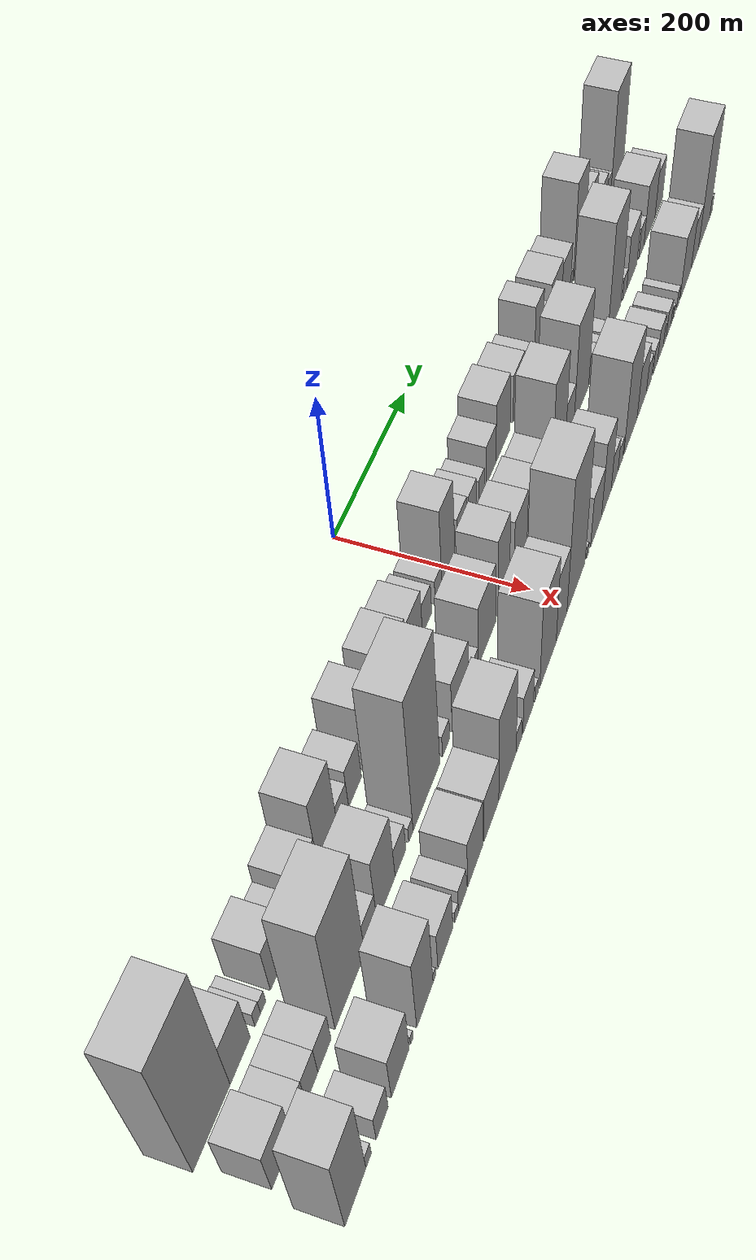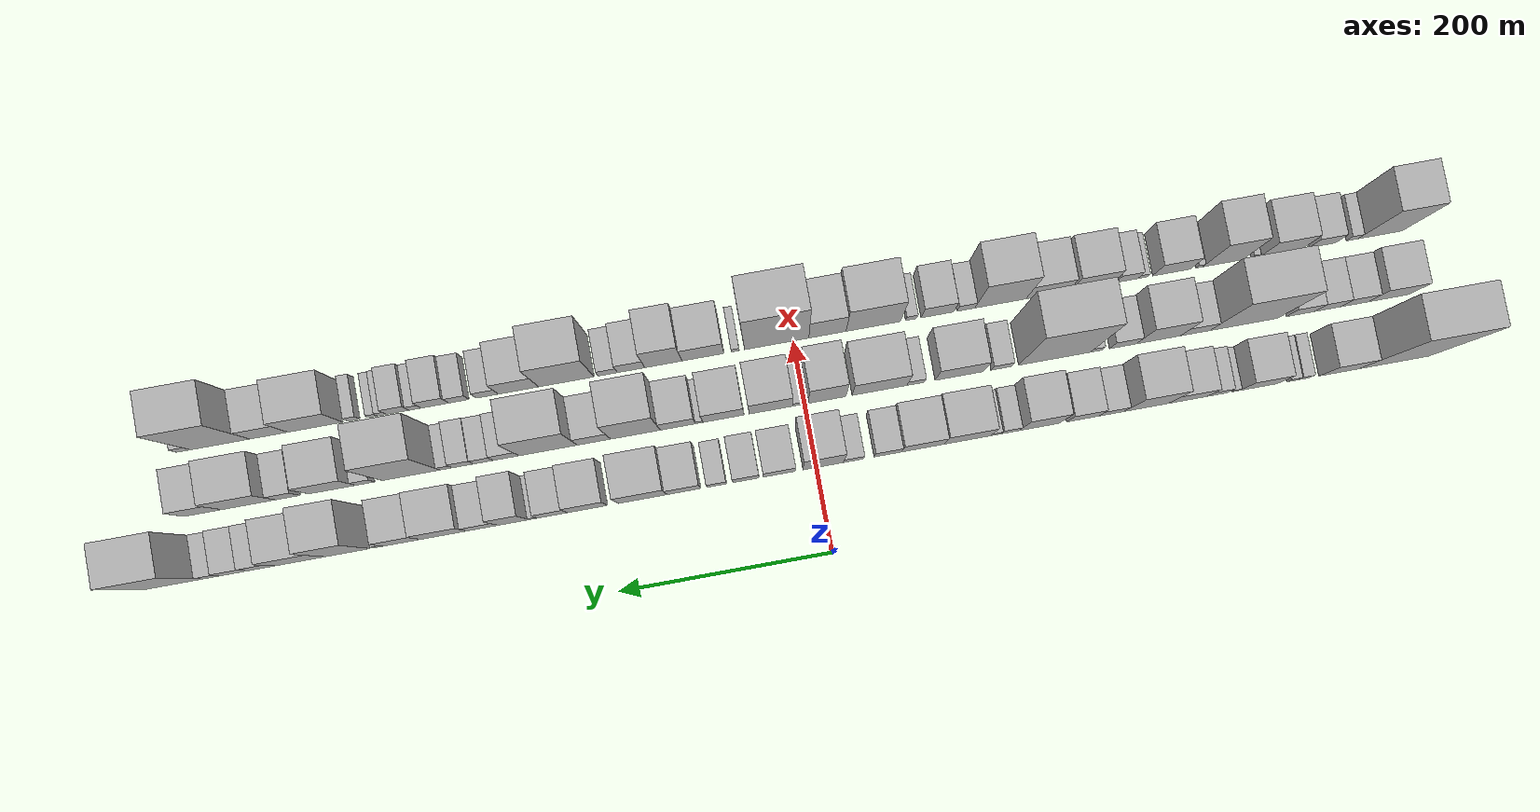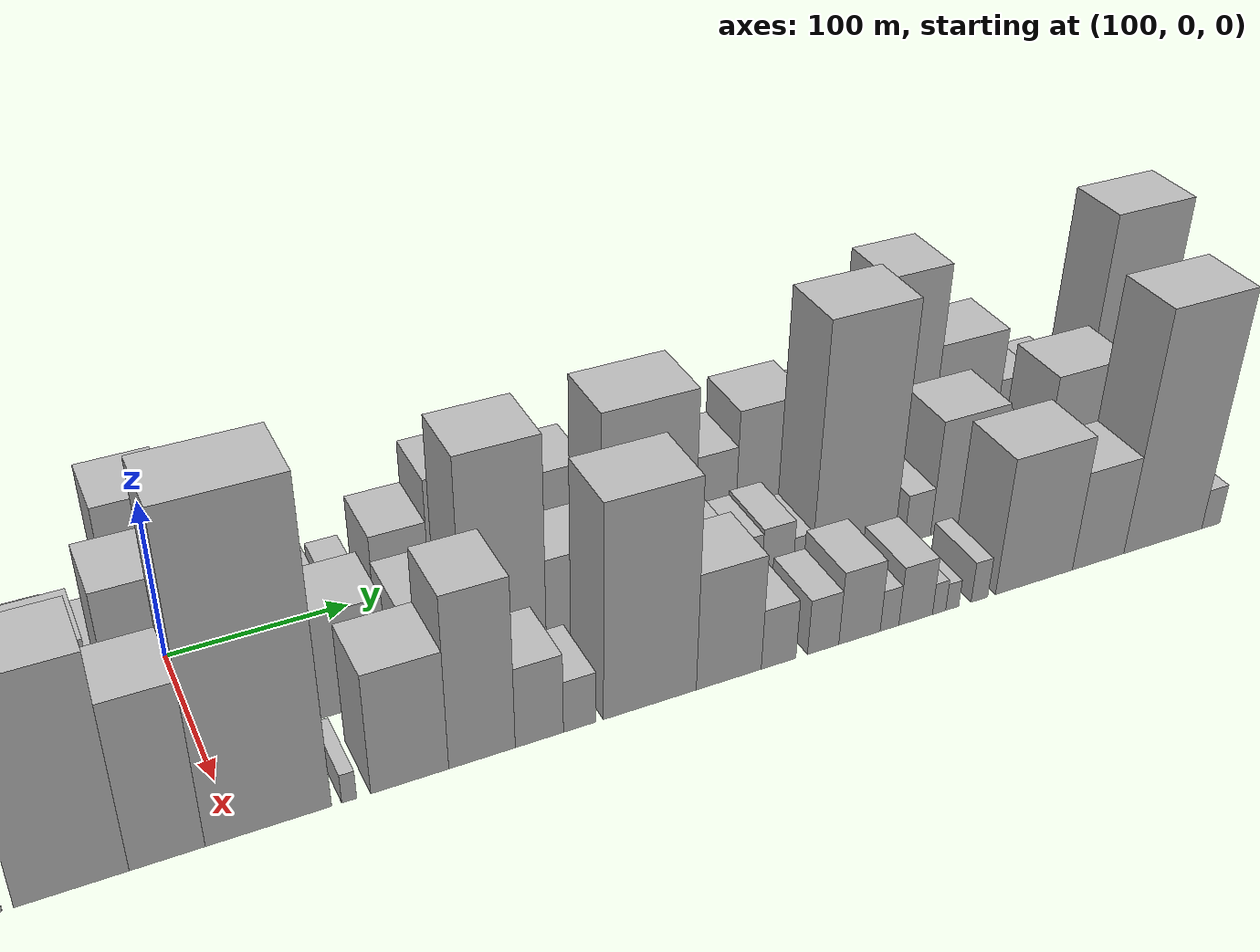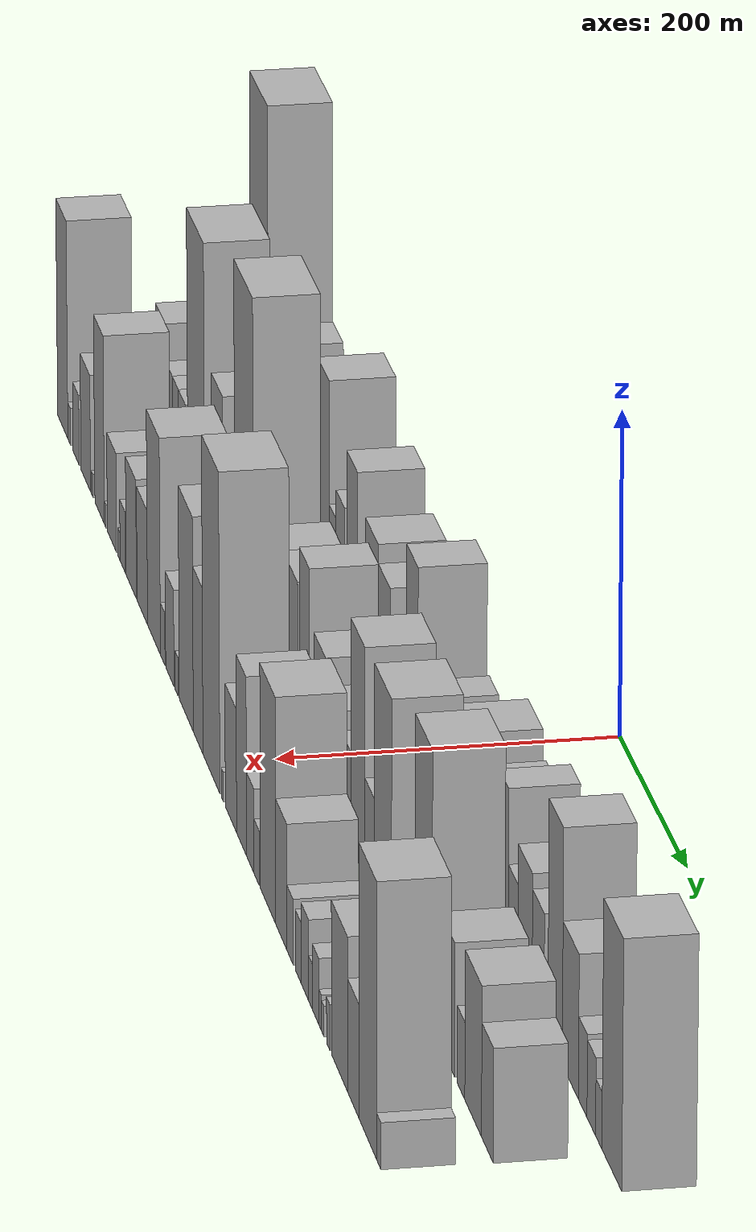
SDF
<sdf version="1.6">
 <world name="default">
  <scene>
   <sky><clouds><speed>12</speed></clouds></sky>
   <ambient>0.4 0.4 0.4 1</ambient>
   <background>0.7 0.7 0.7 1</background>
   <shadows>1</shadows>
  </scene>
  <gravity>0 0 -9.8066</gravity>
  <magnetic_field>6e-06 2.3e-05 -4.2e-05</magnetic_field>
  <physics default="0" name="default_physics" type="ode">
   <ode>
    <solver>
     <type>quick</type>
     <iters>10</iters>
     <sor>1.0</sor>
     <use_dynamic_moi_rescaling>0</use_dynamic_moi_rescaling>
    </solver>
    <constraints>
     <cfm>0</cfm>
     <erp>0.2</erp>
     <contact_max_correcting_vel>100</contact_max_correcting_vel>
     <contact_surface_layer>0.001</contact_surface_layer>
    </constraints>
   </ode>
   <max_step_size>0.004</max_step_size>
   <real_time_factor>1</real_time_factor>
   <real_time_update_rate>250</real_time_update_rate>
  </physics>
  <light name="sun" type="directional">
   <pose>0 0 10 0 0 0</pose>
   <diffuse>0.8 0.8 0.8 1</diffuse>
   <specular>0.2 0.2 0.2 1</specular>
   <attenuation>
    <range>1000</range>
    <constant>0.9</constant>
    <linear>0.01</linear>
    <quadratic>0.001</quadratic>
   </attenuation>
   <direction>-0.5 0.1 -0.9</direction>
  </light>
  <model name="building_1">
   <static>1</static>
   <pose>100.0000 -546.4433 0 0.000000 0.000000 0.000000</pose>
   <link name="link">
    <pose>0 0 108.00 0 0 0</pose>
    <collision name="collision"><geometry><box><size>40.0000 67.1135 216.0000</size></box></geometry></collision>
    <visual name="visual">
     <cast_shadows>0</cast_shadows>
     <geometry><box><size>40.0000 67.1135 216.0000</size></box></geometry>
     <material>
      <script>
       <uri>model://HANNAS_wall/materials/scripts</uri>
       <uri>model://HANNAS_wall/materials/textures</uri>
       <name>vrc/HANNAS_wall</name>
      </script>
     </material>
    </visual>
   </link>
  </model>
  <model name="building_2">
   <static>1</static>
   <pose>100.0000 -493.9066 0 0.000000 0.000000 0.000000</pose>
   <link name="link">
    <pose>0 0 37.50 0 0 0</pose>
    <collision name="collision"><geometry><box><size>40.0000 37.9599 75.0000</size></box></geometry></collision>
    <visual name="visual">
     <cast_shadows>0</cast_shadows>
     <geometry><box><size>40.0000 37.9599 75.0000</size></box></geometry>
     <material>
      <script>
       <uri>model://HANNAS_wall/materials/scripts</uri>
       <uri>model://HANNAS_wall/materials/textures</uri>
       <name>vrc/HANNAS_wall</name>
      </script>
     </material>
    </visual>
   </link>
  </model>
  <model name="building_3">
   <static>1</static>
   <pose>100.0000 -460.3726 0 0.000000 0.000000 0.000000</pose>
   <link name="link">
    <pose>0 0 12.00 0 0 0</pose>
    <collision name="collision"><geometry><box><size>40.0000 11.1080 24.0000</size></box></geometry></collision>
    <visual name="visual">
     <cast_shadows>0</cast_shadows>
     <geometry><box><size>40.0000 11.1080 24.0000</size></box></geometry>
     <material>
      <script>
       <uri>model://HANNAS_wall/materials/scripts</uri>
       <uri>model://HANNAS_wall/materials/textures</uri>
       <name>vrc/HANNAS_wall</name>
      </script>
     </material>
    </visual>
   </link>
  </model>
  <model name="building_4">
   <static>1</static>
   <pose>100.0000 -449.6545 0 0.000000 0.000000 0.000000</pose>
   <link name="link">
    <pose>0 0 10.50 0 0 0</pose>
    <collision name="collision"><geometry><box><size>40.0000 10.3283 21.0000</size></box></geometry></collision>
    <visual name="visual">
     <cast_shadows>0</cast_shadows>
     <geometry><box><size>40.0000 10.3283 21.0000</size></box></geometry>
     <material>
      <script>
       <uri>model://HANNAS_wall/materials/scripts</uri>
       <uri>model://HANNAS_wall/materials/textures</uri>
       <name>vrc/HANNAS_wall</name>
      </script>
     </material>
    </visual>
   </link>
  </model>
  <model name="building_5">
   <static>1</static>
   <pose>100.0000 -417.2643 0 0.000000 0.000000 0.000000</pose>
   <link name="link">
    <pose>0 0 36.00 0 0 0</pose>
    <collision name="collision"><geometry><box><size>40.0000 36.4522 72.0000</size></box></geometry></collision>
    <visual name="visual">
     <cast_shadows>0</cast_shadows>
     <geometry><box><size>40.0000 36.4522 72.0000</size></box></geometry>
     <material>
      <script>
       <uri>model://HANNAS_wall/materials/scripts</uri>
       <uri>model://HANNAS_wall/materials/textures</uri>
       <name>vrc/HANNAS_wall</name>
      </script>
     </material>
    </visual>
   </link>
  </model>
  <model name="building_6">
   <static>1</static>
   <pose>100.0000 -395.6459 0 0.000000 0.000000 0.000000</pose>
   <link name="link">
    <pose>0 0 7.50 0 0 0</pose>
    <collision name="collision"><geometry><box><size>40.0000 6.7845 15.0000</size></box></geometry></collision>
    <visual name="visual">
     <cast_shadows>0</cast_shadows>
     <geometry><box><size>40.0000 6.7845 15.0000</size></box></geometry>
     <material>
      <script>
       <uri>model://HANNAS_wall/materials/scripts</uri>
       <uri>model://HANNAS_wall/materials/textures</uri>
       <name>vrc/HANNAS_wall</name>
      </script>
     </material>
    </visual>
   </link>
  </model>
  <model name="building_7">
   <static>1</static>
   <pose>100.0000 -378.6369 0 0.000000 0.000000 0.000000</pose>
   <link name="link">
    <pose>0 0 18.00 0 0 0</pose>
    <collision name="collision"><geometry><box><size>40.0000 19.2335 36.0000</size></box></geometry></collision>
    <visual name="visual">
     <cast_shadows>0</cast_shadows>
     <geometry><box><size>40.0000 19.2335 36.0000</size></box></geometry>
     <material>
      <script>
       <uri>model://HANNAS_wall/materials/scripts</uri>
       <uri>model://HANNAS_wall/materials/textures</uri>
       <name>vrc/HANNAS_wall</name>
      </script>
     </material>
    </visual>
   </link>
  </model>
  <model name="building_8">
   <static>1</static>
   <pose>100.0000 -350.5014 0 0.000000 0.000000 0.000000</pose>
   <link name="link">
    <pose>0 0 33.00 0 0 0</pose>
    <collision name="collision"><geometry><box><size>40.0000 37.0376 66.0000</size></box></geometry></collision>
    <visual name="visual">
     <cast_shadows>0</cast_shadows>
     <geometry><box><size>40.0000 37.0376 66.0000</size></box></geometry>
     <material>
      <script>
       <uri>model://HANNAS_wall/materials/scripts</uri>
       <uri>model://HANNAS_wall/materials/textures</uri>
       <name>vrc/HANNAS_wall</name>
      </script>
     </material>
    </visual>
   </link>
  </model>
  <model name="building_9">
   <static>1</static>
   <pose>100.0000 -311.1250 0 0.000000 0.000000 0.000000</pose>
   <link name="link">
    <pose>0 0 60.00 0 0 0</pose>
    <collision name="collision"><geometry><box><size>40.0000 41.7151 120.0000</size></box></geometry></collision>
    <visual name="visual">
     <cast_shadows>0</cast_shadows>
     <geometry><box><size>40.0000 41.7151 120.0000</size></box></geometry>
     <material>
      <script>
       <uri>model://HANNAS_wall/materials/scripts</uri>
       <uri>model://HANNAS_wall/materials/textures</uri>
       <name>vrc/HANNAS_wall</name>
      </script>
     </material>
    </visual>
   </link>
  </model>
  <model name="building_10">
   <static>1</static>
   <pose>100.0000 -278.2052 0 0.000000 0.000000 0.000000</pose>
   <link name="link">
    <pose>0 0 21.00 0 0 0</pose>
    <collision name="collision"><geometry><box><size>40.0000 24.1245 42.0000</size></box></geometry></collision>
    <visual name="visual">
     <cast_shadows>0</cast_shadows>
     <geometry><box><size>40.0000 24.1245 42.0000</size></box></geometry>
     <material>
      <script>
       <uri>model://HANNAS_wall/materials/scripts</uri>
       <uri>model://HANNAS_wall/materials/textures</uri>
       <name>vrc/HANNAS_wall</name>
      </script>
     </material>
    </visual>
   </link>
  </model>
  <model name="building_11">
   <static>1</static>
   <pose>100.0000 -250.9909 0 0.000000 0.000000 0.000000</pose>
   <link name="link">
    <pose>0 0 30.00 0 0 0</pose>
    <collision name="collision"><geometry><box><size>40.0000 30.3041 60.0000</size></box></geometry></collision>
    <visual name="visual">
     <cast_shadows>0</cast_shadows>
     <geometry><box><size>40.0000 30.3041 60.0000</size></box></geometry>
     <material>
      <script>
       <uri>model://HANNAS_wall/materials/scripts</uri>
       <uri>model://HANNAS_wall/materials/textures</uri>
       <name>vrc/HANNAS_wall</name>
      </script>
     </material>
    </visual>
   </link>
  </model>
  <model name="building_12">
   <static>1</static>
   <pose>100.0000 -209.8831 0 0.000000 0.000000 0.000000</pose>
   <link name="link">
    <pose>0 0 49.50 0 0 0</pose>
    <collision name="collision"><geometry><box><size>40.0000 37.9116 99.0000</size></box></geometry></collision>
    <visual name="visual">
     <cast_shadows>0</cast_shadows>
     <geometry><box><size>40.0000 37.9116 99.0000</size></box></geometry>
     <material>
      <script>
       <uri>model://HANNAS_wall/materials/scripts</uri>
       <uri>model://HANNAS_wall/materials/textures</uri>
       <name>vrc/HANNAS_wall</name>
      </script>
     </material>
    </visual>
   </link>
  </model>
  <model name="building_13">
   <static>1</static>
   <pose>100.0000 -182.4297 0 0.000000 0.000000 0.000000</pose>
   <link name="link">
    <pose>0 0 16.50 0 0 0</pose>
    <collision name="collision"><geometry><box><size>40.0000 16.9952 33.0000</size></box></geometry></collision>
    <visual name="visual">
     <cast_shadows>0</cast_shadows>
     <geometry><box><size>40.0000 16.9952 33.0000</size></box></geometry>
     <material>
      <script>
       <uri>model://HANNAS_wall/materials/scripts</uri>
       <uri>model://HANNAS_wall/materials/textures</uri>
       <name>vrc/HANNAS_wall</name>
      </script>
     </material>
    </visual>
   </link>
  </model>
  <model name="building_14">
   <static>1</static>
   <pose>100.0000 -169.0373 0 0.000000 0.000000 0.000000</pose>
   <link name="link">
    <pose>0 0 10.50 0 0 0</pose>
    <collision name="collision"><geometry><box><size>40.0000 9.7896 21.0000</size></box></geometry></collision>
    <visual name="visual">
     <cast_shadows>0</cast_shadows>
     <geometry><box><size>40.0000 9.7896 21.0000</size></box></geometry>
     <material>
      <script>
       <uri>model://HANNAS_wall/materials/scripts</uri>
       <uri>model://HANNAS_wall/materials/textures</uri>
       <name>vrc/HANNAS_wall</name>
      </script>
     </material>
    </visual>
   </link>
  </model>
  <model name="building_15">
   <static>1</static>
   <pose>100.0000 -141.9730 0 0.000000 0.000000 0.000000</pose>
   <link name="link">
    <pose>0 0 40.50 0 0 0</pose>
    <collision name="collision"><geometry><box><size>40.0000 44.3388 81.0000</size></box></geometry></collision>
    <visual name="visual">
     <cast_shadows>0</cast_shadows>
     <geometry><box><size>40.0000 44.3388 81.0000</size></box></geometry>
     <material>
      <script>
       <uri>model://HANNAS_wall/materials/scripts</uri>
       <uri>model://HANNAS_wall/materials/textures</uri>
       <name>vrc/HANNAS_wall</name>
      </script>
     </material>
    </visual>
   </link>
  </model>
  <model name="building_16">
   <static>1</static>
   <pose>100.0000 -99.6615 0 0.000000 0.000000 0.000000</pose>
   <link name="link">
    <pose>0 0 34.50 0 0 0</pose>
    <collision name="collision"><geometry><box><size>40.0000 40.2842 69.0000</size></box></geometry></collision>
    <visual name="visual">
     <cast_shadows>0</cast_shadows>
     <geometry><box><size>40.0000 40.2842 69.0000</size></box></geometry>
     <material>
      <script>
       <uri>model://HANNAS_wall/materials/scripts</uri>
       <uri>model://HANNAS_wall/materials/textures</uri>
       <name>vrc/HANNAS_wall</name>
      </script>
     </material>
    </visual>
   </link>
  </model>
  <model name="building_17">
   <static>1</static>
   <pose>100.0000 -66.7461 0 0.000000 0.000000 0.000000</pose>
   <link name="link">
    <pose>0 0 22.50 0 0 0</pose>
    <collision name="collision"><geometry><box><size>40.0000 25.5467 45.0000</size></box></geometry></collision>
    <visual name="visual">
     <cast_shadows>0</cast_shadows>
     <geometry><box><size>40.0000 25.5467 45.0000</size></box></geometry>
     <material>
      <script>
       <uri>model://HANNAS_wall/materials/scripts</uri>
       <uri>model://HANNAS_wall/materials/textures</uri>
       <name>vrc/HANNAS_wall</name>
      </script>
     </material>
    </visual>
   </link>
  </model>
  <model name="building_18">
   <static>1</static>
   <pose>100.0000 -34.4902 0 0.000000 0.000000 0.000000</pose>
   <link name="link">
    <pose>0 0 18.00 0 0 0</pose>
    <collision name="collision"><geometry><box><size>40.0000 18.9651 36.0000</size></box></geometry></collision>
    <visual name="visual">
     <cast_shadows>0</cast_shadows>
     <geometry><box><size>40.0000 18.9651 36.0000</size></box></geometry>
     <material>
      <script>
       <uri>model://HANNAS_wall/materials/scripts</uri>
       <uri>model://HANNAS_wall/materials/textures</uri>
       <name>vrc/HANNAS_wall</name>
      </script>
     </material>
    </visual>
   </link>
  </model>
  <model name="building_19">
   <static>1</static>
   <pose>100.0000 -6.0359 0 0.000000 0.000000 0.000000</pose>
   <link name="link">
    <pose>0 0 58.50 0 0 0</pose>
    <collision name="collision"><geometry><box><size>40.0000 37.9435 117.0000</size></box></geometry></collision>
    <visual name="visual">
     <cast_shadows>0</cast_shadows>
     <geometry><box><size>40.0000 37.9435 117.0000</size></box></geometry>
     <material>
      <script>
       <uri>model://HANNAS_wall/materials/scripts</uri>
       <uri>model://HANNAS_wall/materials/textures</uri>
       <name>vrc/HANNAS_wall</name>
      </script>
     </material>
    </visual>
   </link>
  </model>
  <model name="building_20">
   <static>1</static>
   <pose>100.0000 35.0194 0 0.000000 0.000000 0.000000</pose>
   <link name="link">
    <pose>0 0 25.50 0 0 0</pose>
    <collision name="collision"><geometry><box><size>40.0000 30.1672 51.0000</size></box></geometry></collision>
    <visual name="visual">
     <cast_shadows>0</cast_shadows>
     <geometry><box><size>40.0000 30.1672 51.0000</size></box></geometry>
     <material>
      <script>
       <uri>model://HANNAS_wall/materials/scripts</uri>
       <uri>model://HANNAS_wall/materials/textures</uri>
       <name>vrc/HANNAS_wall</name>
      </script>
     </material>
    </visual>
   </link>
  </model>
  <model name="building_21">
   <static>1</static>
   <pose>100.0000 66.4379 0 0.000000 0.000000 0.000000</pose>
   <link name="link">
    <pose>0 0 22.50 0 0 0</pose>
    <collision name="collision"><geometry><box><size>40.0000 24.6696 45.0000</size></box></geometry></collision>
    <visual name="visual">
     <cast_shadows>0</cast_shadows>
     <geometry><box><size>40.0000 24.6696 45.0000</size></box></geometry>
     <material>
      <script>
       <uri>model://HANNAS_wall/materials/scripts</uri>
       <uri>model://HANNAS_wall/materials/textures</uri>
       <name>vrc/HANNAS_wall</name>
      </script>
     </material>
    </visual>
   </link>
  </model>
  <model name="building_22">
   <static>1</static>
   <pose>100.0000 93.9108 0 0.000000 0.000000 0.000000</pose>
   <link name="link">
    <pose>0 0 16.50 0 0 0</pose>
    <collision name="collision"><geometry><box><size>40.0000 18.2762 33.0000</size></box></geometry></collision>
    <visual name="visual">
     <cast_shadows>0</cast_shadows>
     <geometry><box><size>40.0000 18.2762 33.0000</size></box></geometry>
     <material>
      <script>
       <uri>model://HANNAS_wall/materials/scripts</uri>
       <uri>model://HANNAS_wall/materials/textures</uri>
       <name>vrc/HANNAS_wall</name>
      </script>
     </material>
    </visual>
   </link>
  </model>
  <model name="building_23">
   <static>1</static>
   <pose>100.0000 124.8384 0 0.000000 0.000000 0.000000</pose>
   <link name="link">
    <pose>0 0 28.50 0 0 0</pose>
    <collision name="collision"><geometry><box><size>40.0000 31.5791 57.0000</size></box></geometry></collision>
    <visual name="visual">
     <cast_shadows>0</cast_shadows>
     <geometry><box><size>40.0000 31.5791 57.0000</size></box></geometry>
     <material>
      <script>
       <uri>model://HANNAS_wall/materials/scripts</uri>
       <uri>model://HANNAS_wall/materials/textures</uri>
       <name>vrc/HANNAS_wall</name>
      </script>
     </material>
    </visual>
   </link>
  </model>
  <model name="building_24">
   <static>1</static>
   <pose>100.0000 163.6216 0 0.000000 0.000000 0.000000</pose>
   <link name="link">
    <pose>0 0 42.00 0 0 0</pose>
    <collision name="collision"><geometry><box><size>40.0000 45.9873 84.0000</size></box></geometry></collision>
    <visual name="visual">
     <cast_shadows>0</cast_shadows>
     <geometry><box><size>40.0000 45.9873 84.0000</size></box></geometry>
     <material>
      <script>
       <uri>model://HANNAS_wall/materials/scripts</uri>
       <uri>model://HANNAS_wall/materials/textures</uri>
       <name>vrc/HANNAS_wall</name>
      </script>
     </material>
    </visual>
   </link>
  </model>
  <model name="building_25">
   <static>1</static>
   <pose>100.0000 215.3193 0 0.000000 0.000000 0.000000</pose>
   <link name="link">
    <pose>0 0 34.50 0 0 0</pose>
    <collision name="collision"><geometry><box><size>40.0000 37.4080 69.0000</size></box></geometry></collision>
    <visual name="visual">
     <cast_shadows>0</cast_shadows>
     <geometry><box><size>40.0000 37.4080 69.0000</size></box></geometry>
     <material>
      <script>
       <uri>model://HANNAS_wall/materials/scripts</uri>
       <uri>model://HANNAS_wall/materials/textures</uri>
       <name>vrc/HANNAS_wall</name>
      </script>
     </material>
    </visual>
   </link>
  </model>
  <model name="building_26">
   <static>1</static>
   <pose>100.0000 247.8626 0 0.000000 0.000000 0.000000</pose>
   <link name="link">
    <pose>0 0 27.00 0 0 0</pose>
    <collision name="collision"><geometry><box><size>40.0000 27.6784 54.0000</size></box></geometry></collision>
    <visual name="visual">
     <cast_shadows>0</cast_shadows>
     <geometry><box><size>40.0000 27.6784 54.0000</size></box></geometry>
     <material>
      <script>
       <uri>model://HANNAS_wall/materials/scripts</uri>
       <uri>model://HANNAS_wall/materials/textures</uri>
       <name>vrc/HANNAS_wall</name>
      </script>
     </material>
    </visual>
   </link>
  </model>
  <model name="building_27">
   <static>1</static>
   <pose>100.0000 265.8495 0 0.000000 0.000000 0.000000</pose>
   <link name="link">
    <pose>0 0 9.00 0 0 0</pose>
    <collision name="collision"><geometry><box><size>40.0000 8.2954 18.0000</size></box></geometry></collision>
    <visual name="visual">
     <cast_shadows>0</cast_shadows>
     <geometry><box><size>40.0000 8.2954 18.0000</size></box></geometry>
     <material>
      <script>
       <uri>model://HANNAS_wall/materials/scripts</uri>
       <uri>model://HANNAS_wall/materials/textures</uri>
       <name>vrc/HANNAS_wall</name>
      </script>
     </material>
    </visual>
   </link>
  </model>
  <model name="building_28">
   <static>1</static>
   <pose>100.0000 284.5467 0 0.000000 0.000000 0.000000</pose>
   <link name="link">
    <pose>0 0 48.00 0 0 0</pose>
    <collision name="collision"><geometry><box><size>40.0000 29.0990 96.0000</size></box></geometry></collision>
    <visual name="visual">
     <cast_shadows>0</cast_shadows>
     <geometry><box><size>40.0000 29.0990 96.0000</size></box></geometry>
     <material>
      <script>
       <uri>model://HANNAS_wall/materials/scripts</uri>
       <uri>model://HANNAS_wall/materials/textures</uri>
       <name>vrc/HANNAS_wall</name>
      </script>
     </material>
    </visual>
   </link>
  </model>
  <model name="building_29">
   <static>1</static>
   <pose>100.0000 313.6261 0 0.000000 0.000000 0.000000</pose>
   <link name="link">
    <pose>0 0 25.50 0 0 0</pose>
    <collision name="collision"><geometry><box><size>40.0000 29.0598 51.0000</size></box></geometry></collision>
    <visual name="visual">
     <cast_shadows>0</cast_shadows>
     <geometry><box><size>40.0000 29.0598 51.0000</size></box></geometry>
     <material>
      <script>
       <uri>model://HANNAS_wall/materials/scripts</uri>
       <uri>model://HANNAS_wall/materials/textures</uri>
       <name>vrc/HANNAS_wall</name>
      </script>
     </material>
    </visual>
   </link>
  </model>
  <model name="building_30">
   <static>1</static>
   <pose>100.0000 349.7752 0 0.000000 0.000000 0.000000</pose>
   <link name="link">
    <pose>0 0 37.50 0 0 0</pose>
    <collision name="collision"><geometry><box><size>40.0000 43.2384 75.0000</size></box></geometry></collision>
    <visual name="visual">
     <cast_shadows>0</cast_shadows>
     <geometry><box><size>40.0000 43.2384 75.0000</size></box></geometry>
     <material>
      <script>
       <uri>model://HANNAS_wall/materials/scripts</uri>
       <uri>model://HANNAS_wall/materials/textures</uri>
       <name>vrc/HANNAS_wall</name>
      </script>
     </material>
    </visual>
   </link>
  </model>
  <model name="building_31">
   <static>1</static>
   <pose>100.0000 389.1786 0 0.000000 0.000000 0.000000</pose>
   <link name="link">
    <pose>0 0 33.00 0 0 0</pose>
    <collision name="collision"><geometry><box><size>40.0000 35.5685 66.0000</size></box></geometry></collision>
    <visual name="visual">
     <cast_shadows>0</cast_shadows>
     <geometry><box><size>40.0000 35.5685 66.0000</size></box></geometry>
     <material>
      <script>
       <uri>model://HANNAS_wall/materials/scripts</uri>
       <uri>model://HANNAS_wall/materials/textures</uri>
       <name>vrc/HANNAS_wall</name>
      </script>
     </material>
    </visual>
   </link>
  </model>
  <model name="building_32">
   <static>1</static>
   <pose>100.0000 411.1908 0 0.000000 0.000000 0.000000</pose>
   <link name="link">
    <pose>0 0 10.50 0 0 0</pose>
    <collision name="collision"><geometry><box><size>40.0000 8.4559 21.0000</size></box></geometry></collision>
    <visual name="visual">
     <cast_shadows>0</cast_shadows>
     <geometry><box><size>40.0000 8.4559 21.0000</size></box></geometry>
     <material>
      <script>
       <uri>model://HANNAS_wall/materials/scripts</uri>
       <uri>model://HANNAS_wall/materials/textures</uri>
       <name>vrc/HANNAS_wall</name>
      </script>
     </material>
    </visual>
   </link>
  </model>
  <model name="building_33">
   <static>1</static>
   <pose>100.0000 439.5390 0 0.000000 0.000000 0.000000</pose>
   <link name="link">
    <pose>0 0 69.00 0 0 0</pose>
    <collision name="collision"><geometry><box><size>40.0000 42.2405 138.0000</size></box></geometry></collision>
    <visual name="visual">
     <cast_shadows>0</cast_shadows>
     <geometry><box><size>40.0000 42.2405 138.0000</size></box></geometry>
     <material>
      <script>
       <uri>model://HANNAS_wall/materials/scripts</uri>
       <uri>model://HANNAS_wall/materials/textures</uri>
       <name>vrc/HANNAS_wall</name>
      </script>
     </material>
    </visual>
   </link>
  </model>
  <model name="building_34">
   <static>1</static>
   <pose>100.0000 483.9967 0 0.000000 0.000000 0.000000</pose>
   <link name="link">
    <pose>0 0 42.00 0 0 0</pose>
    <collision name="collision"><geometry><box><size>40.0000 46.6749 84.0000</size></box></geometry></collision>
    <visual name="visual">
     <cast_shadows>0</cast_shadows>
     <geometry><box><size>40.0000 46.6749 84.0000</size></box></geometry>
     <material>
      <script>
       <uri>model://HANNAS_wall/materials/scripts</uri>
       <uri>model://HANNAS_wall/materials/textures</uri>
       <name>vrc/HANNAS_wall</name>
      </script>
     </material>
    </visual>
   </link>
  </model>
  <model name="building_35">
   <static>1</static>
   <pose>100.0000 519.7663 0 0.000000 0.000000 0.000000</pose>
   <link name="link">
    <pose>0 0 24.00 0 0 0</pose>
    <collision name="collision"><geometry><box><size>40.0000 24.8643 48.0000</size></box></geometry></collision>
    <visual name="visual">
     <cast_shadows>0</cast_shadows>
     <geometry><box><size>40.0000 24.8643 48.0000</size></box></geometry>
     <material>
      <script>
       <uri>model://HANNAS_wall/materials/scripts</uri>
       <uri>model://HANNAS_wall/materials/textures</uri>
       <name>vrc/HANNAS_wall</name>
      </script>
     </material>
    </visual>
   </link>
  </model>
  <model name="building_36">
   <static>1</static>
   <pose>100.0000 544.4807 0 0.000000 0.000000 0.000000</pose>
   <link name="link">
    <pose>0 0 22.50 0 0 0</pose>
    <collision name="collision"><geometry><box><size>40.0000 24.5645 45.0000</size></box></geometry></collision>
    <visual name="visual">
     <cast_shadows>0</cast_shadows>
     <geometry><box><size>40.0000 24.5645 45.0000</size></box></geometry>
     <material>
      <script>
       <uri>model://HANNAS_wall/materials/scripts</uri>
       <uri>model://HANNAS_wall/materials/textures</uri>
       <name>vrc/HANNAS_wall</name>
      </script>
     </material>
    </visual>
   </link>
  </model>
  <model name="building_37">
   <static>1</static>
   <pose>100.0000 565.7648 0 0.000000 0.000000 0.000000</pose>
   <link name="link">
    <pose>0 0 16.50 0 0 0</pose>
    <collision name="collision"><geometry><box><size>40.0000 18.0036 33.0000</size></box></geometry></collision>
    <visual name="visual">
     <cast_shadows>0</cast_shadows>
     <geometry><box><size>40.0000 18.0036 33.0000</size></box></geometry>
     <material>
      <script>
       <uri>model://HANNAS_wall/materials/scripts</uri>
       <uri>model://HANNAS_wall/materials/textures</uri>
       <name>vrc/HANNAS_wall</name>
      </script>
     </material>
    </visual>
   </link>
  </model>
  <model name="building_38">
   <static>1</static>
   <pose>100.0000 602.6879 0 0.000000 0.000000 0.000000</pose>
   <link name="link">
    <pose>0 0 72.00 0 0 0</pose>
    <collision name="collision"><geometry><box><size>40.0000 55.8427 144.0000</size></box></geometry></collision>
    <visual name="visual">
     <cast_shadows>0</cast_shadows>
     <geometry><box><size>40.0000 55.8427 144.0000</size></box></geometry>
     <material>
      <script>
       <uri>model://HANNAS_wall/materials/scripts</uri>
       <uri>model://HANNAS_wall/materials/textures</uri>
       <name>vrc/HANNAS_wall</name>
      </script>
     </material>
    </visual>
   </link>
  </model>
  <model name="building_39">
   <static>1</static>
   <pose>160.0000 -553.6835 0 0.000000 0.000000 0.000000</pose>
   <link name="link">
    <pose>0 0 36.00 0 0 0</pose>
    <collision name="collision"><geometry><box><size>40.0000 38.6329 72.0000</size></box></geometry></collision>
    <visual name="visual">
     <cast_shadows>0</cast_shadows>
     <geometry><box><size>40.0000 38.6329 72.0000</size></box></geometry>
     <material>
      <script>
       <uri>model://HANNAS_wall/materials/scripts</uri>
       <uri>model://HANNAS_wall/materials/textures</uri>
       <name>vrc/HANNAS_wall</name>
      </script>
     </material>
    </visual>
   </link>
  </model>
  <model name="building_40">
   <static>1</static>
   <pose>160.0000 -521.0328 0 0.000000 0.000000 0.000000</pose>
   <link name="link">
    <pose>0 0 24.00 0 0 0</pose>
    <collision name="collision"><geometry><box><size>40.0000 26.6685 48.0000</size></box></geometry></collision>
    <visual name="visual">
     <cast_shadows>0</cast_shadows>
     <geometry><box><size>40.0000 26.6685 48.0000</size></box></geometry>
     <material>
      <script>
       <uri>model://HANNAS_wall/materials/scripts</uri>
       <uri>model://HANNAS_wall/materials/textures</uri>
       <name>vrc/HANNAS_wall</name>
      </script>
     </material>
    </visual>
   </link>
  </model>
  <model name="building_41">
   <static>1</static>
   <pose>160.0000 -495.6053 0 0.000000 0.000000 0.000000</pose>
   <link name="link">
    <pose>0 0 24.00 0 0 0</pose>
    <collision name="collision"><geometry><box><size>40.0000 24.1866 48.0000</size></box></geometry></collision>
    <visual name="visual">
     <cast_shadows>0</cast_shadows>
     <geometry><box><size>40.0000 24.1866 48.0000</size></box></geometry>
     <material>
      <script>
       <uri>model://HANNAS_wall/materials/scripts</uri>
       <uri>model://HANNAS_wall/materials/textures</uri>
       <name>vrc/HANNAS_wall</name>
      </script>
     </material>
    </visual>
   </link>
  </model>
  <model name="building_42">
   <static>1</static>
   <pose>160.0000 -469.9660 0 0.000000 0.000000 0.000000</pose>
   <link name="link">
    <pose>0 0 24.00 0 0 0</pose>
    <collision name="collision"><geometry><box><size>40.0000 27.0920 48.0000</size></box></geometry></collision>
    <visual name="visual">
     <cast_shadows>0</cast_shadows>
     <geometry><box><size>40.0000 27.0920 48.0000</size></box></geometry>
     <material>
      <script>
       <uri>model://HANNAS_wall/materials/scripts</uri>
       <uri>model://HANNAS_wall/materials/textures</uri>
       <name>vrc/HANNAS_wall</name>
      </script>
     </material>
    </visual>
   </link>
  </model>
  <model name="building_43">
   <static>1</static>
   <pose>160.0000 -416.1447 0 0.000000 0.000000 0.000000</pose>
   <link name="link">
    <pose>0 0 88.50 0 0 0</pose>
    <collision name="collision"><geometry><box><size>40.0000 64.5504 177.0000</size></box></geometry></collision>
    <visual name="visual">
     <cast_shadows>0</cast_shadows>
     <geometry><box><size>40.0000 64.5504 177.0000</size></box></geometry>
     <material>
      <script>
       <uri>model://HANNAS_wall/materials/scripts</uri>
       <uri>model://HANNAS_wall/materials/textures</uri>
       <name>vrc/HANNAS_wall</name>
      </script>
     </material>
    </visual>
   </link>
  </model>
  <model name="building_44">
   <static>1</static>
   <pose>160.0000 -369.8467 0 0.000000 0.000000 0.000000</pose>
   <link name="link">
    <pose>0 0 25.50 0 0 0</pose>
    <collision name="collision"><geometry><box><size>40.0000 28.0455 51.0000</size></box></geometry></collision>
    <visual name="visual">
     <cast_shadows>0</cast_shadows>
     <geometry><box><size>40.0000 28.0455 51.0000</size></box></geometry>
     <material>
      <script>
       <uri>model://HANNAS_wall/materials/scripts</uri>
       <uri>model://HANNAS_wall/materials/textures</uri>
       <name>vrc/HANNAS_wall</name>
      </script>
     </material>
    </visual>
   </link>
  </model>
  <model name="building_45">
   <static>1</static>
   <pose>160.0000 -334.8662 0 0.000000 0.000000 0.000000</pose>
   <link name="link">
    <pose>0 0 52.50 0 0 0</pose>
    <collision name="collision"><geometry><box><size>40.0000 41.9155 105.0000</size></box></geometry></collision>
    <visual name="visual">
     <cast_shadows>0</cast_shadows>
     <geometry><box><size>40.0000 41.9155 105.0000</size></box></geometry>
     <material>
      <script>
       <uri>model://HANNAS_wall/materials/scripts</uri>
       <uri>model://HANNAS_wall/materials/textures</uri>
       <name>vrc/HANNAS_wall</name>
      </script>
     </material>
    </visual>
   </link>
  </model>
  <model name="building_46">
   <static>1</static>
   <pose>160.0000 -301.0513 0 0.000000 0.000000 0.000000</pose>
   <link name="link">
    <pose>0 0 22.50 0 0 0</pose>
    <collision name="collision"><geometry><box><size>40.0000 25.7144 45.0000</size></box></geometry></collision>
    <visual name="visual">
     <cast_shadows>0</cast_shadows>
     <geometry><box><size>40.0000 25.7144 45.0000</size></box></geometry>
     <material>
      <script>
       <uri>model://HANNAS_wall/materials/scripts</uri>
       <uri>model://HANNAS_wall/materials/textures</uri>
       <name>vrc/HANNAS_wall</name>
      </script>
     </material>
    </visual>
   </link>
  </model>
  <model name="building_47">
   <static>1</static>
   <pose>160.0000 -275.7168 0 0.000000 0.000000 0.000000</pose>
   <link name="link">
    <pose>0 0 12.00 0 0 0</pose>
    <collision name="collision"><geometry><box><size>40.0000 10.9546 24.0000</size></box></geometry></collision>
    <visual name="visual">
     <cast_shadows>0</cast_shadows>
     <geometry><box><size>40.0000 10.9546 24.0000</size></box></geometry>
     <material>
      <script>
       <uri>model://HANNAS_wall/materials/scripts</uri>
       <uri>model://HANNAS_wall/materials/textures</uri>
       <name>vrc/HANNAS_wall</name>
      </script>
     </material>
    </visual>
   </link>
  </model>
  <model name="building_48">
   <static>1</static>
   <pose>160.0000 -236.1369 0 0.000000 0.000000 0.000000</pose>
   <link name="link">
    <pose>0 0 103.50 0 0 0</pose>
    <collision name="collision"><geometry><box><size>40.0000 68.2053 207.0000</size></box></geometry></collision>
    <visual name="visual">
     <cast_shadows>0</cast_shadows>
     <geometry><box><size>40.0000 68.2053 207.0000</size></box></geometry>
     <material>
      <script>
       <uri>model://HANNAS_wall/materials/scripts</uri>
       <uri>model://HANNAS_wall/materials/textures</uri>
       <name>vrc/HANNAS_wall</name>
      </script>
     </material>
    </visual>
   </link>
  </model>
  <model name="building_49">
   <static>1</static>
   <pose>160.0000 -185.4264 0 0.000000 0.000000 0.000000</pose>
   <link name="link">
    <pose>0 0 16.50 0 0 0</pose>
    <collision name="collision"><geometry><box><size>40.0000 19.2157 33.0000</size></box></geometry></collision>
    <visual name="visual">
     <cast_shadows>0</cast_shadows>
     <geometry><box><size>40.0000 19.2157 33.0000</size></box></geometry>
     <material>
      <script>
       <uri>model://HANNAS_wall/materials/scripts</uri>
       <uri>model://HANNAS_wall/materials/textures</uri>
       <name>vrc/HANNAS_wall</name>
      </script>
     </material>
    </visual>
   </link>
  </model>
  <model name="building_50">
   <static>1</static>
   <pose>160.0000 -145.8420 0 0.000000 0.000000 0.000000</pose>
   <link name="link">
    <pose>0 0 39.00 0 0 0</pose>
    <collision name="collision"><geometry><box><size>40.0000 45.9530 78.0000</size></box></geometry></collision>
    <visual name="visual">
     <cast_shadows>0</cast_shadows>
     <geometry><box><size>40.0000 45.9530 78.0000</size></box></geometry>
     <material>
      <script>
       <uri>model://HANNAS_wall/materials/scripts</uri>
       <uri>model://HANNAS_wall/materials/textures</uri>
       <name>vrc/HANNAS_wall</name>
      </script>
     </material>
    </visual>
   </link>
  </model>
  <model name="building_51">
   <static>1</static>
   <pose>160.0000 -104.5533 0 0.000000 0.000000 0.000000</pose>
   <link name="link">
    <pose>0 0 15.00 0 0 0</pose>
    <collision name="collision"><geometry><box><size>40.0000 16.6244 30.0000</size></box></geometry></collision>
    <visual name="visual">
     <cast_shadows>0</cast_shadows>
     <geometry><box><size>40.0000 16.6244 30.0000</size></box></geometry>
     <material>
      <script>
       <uri>model://HANNAS_wall/materials/scripts</uri>
       <uri>model://HANNAS_wall/materials/textures</uri>
       <name>vrc/HANNAS_wall</name>
      </script>
     </material>
    </visual>
   </link>
  </model>
  <model name="building_52">
   <static>1</static>
   <pose>160.0000 -70.3179 0 0.000000 0.000000 0.000000</pose>
   <link name="link">
    <pose>0 0 45.00 0 0 0</pose>
    <collision name="collision"><geometry><box><size>40.0000 51.8465 90.0000</size></box></geometry></collision>
    <visual name="visual">
     <cast_shadows>0</cast_shadows>
     <geometry><box><size>40.0000 51.8465 90.0000</size></box></geometry>
     <material>
      <script>
       <uri>model://HANNAS_wall/materials/scripts</uri>
       <uri>model://HANNAS_wall/materials/textures</uri>
       <name>vrc/HANNAS_wall</name>
      </script>
     </material>
    </visual>
   </link>
  </model>
  <model name="building_53">
   <static>1</static>
   <pose>160.0000 -20.6945 0 0.000000 0.000000 0.000000</pose>
   <link name="link">
    <pose>0 0 57.00 0 0 0</pose>
    <collision name="collision"><geometry><box><size>40.0000 35.4002 114.0000</size></box></geometry></collision>
    <visual name="visual">
     <cast_shadows>0</cast_shadows>
     <geometry><box><size>40.0000 35.4002 114.0000</size></box></geometry>
     <material>
      <script>
       <uri>model://HANNAS_wall/materials/scripts</uri>
       <uri>model://HANNAS_wall/materials/textures</uri>
       <name>vrc/HANNAS_wall</name>
      </script>
     </material>
    </visual>
   </link>
  </model>
  <model name="building_54">
   <static>1</static>
   <pose>160.0000 7.2912 0 0.000000 0.000000 0.000000</pose>
   <link name="link">
    <pose>0 0 10.50 0 0 0</pose>
    <collision name="collision"><geometry><box><size>40.0000 8.5712 21.0000</size></box></geometry></collision>
    <visual name="visual">
     <cast_shadows>0</cast_shadows>
     <geometry><box><size>40.0000 8.5712 21.0000</size></box></geometry>
     <material>
      <script>
       <uri>model://HANNAS_wall/materials/scripts</uri>
       <uri>model://HANNAS_wall/materials/textures</uri>
       <name>vrc/HANNAS_wall</name>
      </script>
     </material>
    </visual>
   </link>
  </model>
  <model name="building_55">
   <static>1</static>
   <pose>160.0000 32.0776 0 0.000000 0.000000 0.000000</pose>
   <link name="link">
    <pose>0 0 40.50 0 0 0</pose>
    <collision name="collision"><geometry><box><size>40.0000 41.0017 81.0000</size></box></geometry></collision>
    <visual name="visual">
     <cast_shadows>0</cast_shadows>
     <geometry><box><size>40.0000 41.0017 81.0000</size></box></geometry>
     <material>
      <script>
       <uri>model://HANNAS_wall/materials/scripts</uri>
       <uri>model://HANNAS_wall/materials/textures</uri>
       <name>vrc/HANNAS_wall</name>
      </script>
     </material>
    </visual>
   </link>
  </model>
  <model name="building_56">
   <static>1</static>
   <pose>160.0000 77.0121 0 0.000000 0.000000 0.000000</pose>
   <link name="link">
    <pose>0 0 33.00 0 0 0</pose>
    <collision name="collision"><geometry><box><size>40.0000 38.8673 66.0000</size></box></geometry></collision>
    <visual name="visual">
     <cast_shadows>0</cast_shadows>
     <geometry><box><size>40.0000 38.8673 66.0000</size></box></geometry>
     <material>
      <script>
       <uri>model://HANNAS_wall/materials/scripts</uri>
       <uri>model://HANNAS_wall/materials/textures</uri>
       <name>vrc/HANNAS_wall</name>
      </script>
     </material>
    </visual>
   </link>
  </model>
  <model name="building_57">
   <static>1</static>
   <pose>160.0000 99.9064 0 0.000000 0.000000 0.000000</pose>
   <link name="link">
    <pose>0 0 7.50 0 0 0</pose>
    <collision name="collision"><geometry><box><size>40.0000 6.9213 15.0000</size></box></geometry></collision>
    <visual name="visual">
     <cast_shadows>0</cast_shadows>
     <geometry><box><size>40.0000 6.9213 15.0000</size></box></geometry>
     <material>
      <script>
       <uri>model://HANNAS_wall/materials/scripts</uri>
       <uri>model://HANNAS_wall/materials/textures</uri>
       <name>vrc/HANNAS_wall</name>
      </script>
     </material>
    </visual>
   </link>
  </model>
  <model name="building_58">
   <static>1</static>
   <pose>160.0000 119.9392 0 0.000000 0.000000 0.000000</pose>
   <link name="link">
    <pose>0 0 28.50 0 0 0</pose>
    <collision name="collision"><geometry><box><size>40.0000 33.1442 57.0000</size></box></geometry></collision>
    <visual name="visual">
     <cast_shadows>0</cast_shadows>
     <geometry><box><size>40.0000 33.1442 57.0000</size></box></geometry>
     <material>
      <script>
       <uri>model://HANNAS_wall/materials/scripts</uri>
       <uri>model://HANNAS_wall/materials/textures</uri>
       <name>vrc/HANNAS_wall</name>
      </script>
     </material>
    </visual>
   </link>
  </model>
  <model name="building_59">
   <static>1</static>
   <pose>160.0000 159.8590 0 0.000000 0.000000 0.000000</pose>
   <link name="link">
    <pose>0 0 69.00 0 0 0</pose>
    <collision name="collision"><geometry><box><size>40.0000 46.6953 138.0000</size></box></geometry></collision>
    <visual name="visual">
     <cast_shadows>0</cast_shadows>
     <geometry><box><size>40.0000 46.6953 138.0000</size></box></geometry>
     <material>
      <script>
       <uri>model://HANNAS_wall/materials/scripts</uri>
       <uri>model://HANNAS_wall/materials/textures</uri>
       <name>vrc/HANNAS_wall</name>
      </script>
     </material>
    </visual>
   </link>
  </model>
  <model name="building_60">
   <static>1</static>
   <pose>160.0000 198.9784 0 0.000000 0.000000 0.000000</pose>
   <link name="link">
    <pose>0 0 30.00 0 0 0</pose>
    <collision name="collision"><geometry><box><size>40.0000 31.5436 60.0000</size></box></geometry></collision>
    <visual name="visual">
     <cast_shadows>0</cast_shadows>
     <geometry><box><size>40.0000 31.5436 60.0000</size></box></geometry>
     <material>
      <script>
       <uri>model://HANNAS_wall/materials/scripts</uri>
       <uri>model://HANNAS_wall/materials/textures</uri>
       <name>vrc/HANNAS_wall</name>
      </script>
     </material>
    </visual>
   </link>
  </model>
  <model name="building_61">
   <static>1</static>
   <pose>160.0000 242.1332 0 0.000000 0.000000 0.000000</pose>
   <link name="link">
    <pose>0 0 70.50 0 0 0</pose>
    <collision name="collision"><geometry><box><size>40.0000 54.7659 141.0000</size></box></geometry></collision>
    <visual name="visual">
     <cast_shadows>0</cast_shadows>
     <geometry><box><size>40.0000 54.7659 141.0000</size></box></geometry>
     <material>
      <script>
       <uri>model://HANNAS_wall/materials/scripts</uri>
       <uri>model://HANNAS_wall/materials/textures</uri>
       <name>vrc/HANNAS_wall</name>
      </script>
     </material>
    </visual>
   </link>
  </model>
  <model name="building_62">
   <static>1</static>
   <pose>160.0000 281.5743 0 0.000000 0.000000 0.000000</pose>
   <link name="link">
    <pose>0 0 21.00 0 0 0</pose>
    <collision name="collision"><geometry><box><size>40.0000 24.1162 42.0000</size></box></geometry></collision>
    <visual name="visual">
     <cast_shadows>0</cast_shadows>
     <geometry><box><size>40.0000 24.1162 42.0000</size></box></geometry>
     <material>
      <script>
       <uri>model://HANNAS_wall/materials/scripts</uri>
       <uri>model://HANNAS_wall/materials/textures</uri>
       <name>vrc/HANNAS_wall</name>
      </script>
     </material>
    </visual>
   </link>
  </model>
  <model name="building_63">
   <static>1</static>
   <pose>160.0000 302.7551 0 0.000000 0.000000 0.000000</pose>
   <link name="link">
    <pose>0 0 18.00 0 0 0</pose>
    <collision name="collision"><geometry><box><size>40.0000 18.2454 36.0000</size></box></geometry></collision>
    <visual name="visual">
     <cast_shadows>0</cast_shadows>
     <geometry><box><size>40.0000 18.2454 36.0000</size></box></geometry>
     <material>
      <script>
       <uri>model://HANNAS_wall/materials/scripts</uri>
       <uri>model://HANNAS_wall/materials/textures</uri>
       <name>vrc/HANNAS_wall</name>
      </script>
     </material>
    </visual>
   </link>
  </model>
  <model name="building_64">
   <static>1</static>
   <pose>160.0000 321.8305 0 0.000000 0.000000 0.000000</pose>
   <link name="link">
    <pose>0 0 19.50 0 0 0</pose>
    <collision name="collision"><geometry><box><size>40.0000 19.9054 39.0000</size></box></geometry></collision>
    <visual name="visual">
     <cast_shadows>0</cast_shadows>
     <geometry><box><size>40.0000 19.9054 39.0000</size></box></geometry>
     <material>
      <script>
       <uri>model://HANNAS_wall/materials/scripts</uri>
       <uri>model://HANNAS_wall/materials/textures</uri>
       <name>vrc/HANNAS_wall</name>
      </script>
     </material>
    </visual>
   </link>
  </model>
  <model name="building_65">
   <static>1</static>
   <pose>160.0000 337.7868 0 0.000000 0.000000 0.000000</pose>
   <link name="link">
    <pose>0 0 13.50 0 0 0</pose>
    <collision name="collision"><geometry><box><size>40.0000 12.0073 27.0000</size></box></geometry></collision>
    <visual name="visual">
     <cast_shadows>0</cast_shadows>
     <geometry><box><size>40.0000 12.0073 27.0000</size></box></geometry>
     <material>
      <script>
       <uri>model://HANNAS_wall/materials/scripts</uri>
       <uri>model://HANNAS_wall/materials/textures</uri>
       <name>vrc/HANNAS_wall</name>
      </script>
     </material>
    </visual>
   </link>
  </model>
  <model name="building_66">
   <static>1</static>
   <pose>160.0000 370.8840 0 0.000000 0.000000 0.000000</pose>
   <link name="link">
    <pose>0 0 81.00 0 0 0</pose>
    <collision name="collision"><geometry><box><size>40.0000 54.1870 162.0000</size></box></geometry></collision>
    <visual name="visual">
     <cast_shadows>0</cast_shadows>
     <geometry><box><size>40.0000 54.1870 162.0000</size></box></geometry>
     <material>
      <script>
       <uri>model://HANNAS_wall/materials/scripts</uri>
       <uri>model://HANNAS_wall/materials/textures</uri>
       <name>vrc/HANNAS_wall</name>
      </script>
     </material>
    </visual>
   </link>
  </model>
  <model name="building_67">
   <static>1</static>
   <pose>160.0000 413.7947 0 0.000000 0.000000 0.000000</pose>
   <link name="link">
    <pose>0 0 16.50 0 0 0</pose>
    <collision name="collision"><geometry><box><size>40.0000 17.6344 33.0000</size></box></geometry></collision>
    <visual name="visual">
     <cast_shadows>0</cast_shadows>
     <geometry><box><size>40.0000 17.6344 33.0000</size></box></geometry>
     <material>
      <script>
       <uri>model://HANNAS_wall/materials/scripts</uri>
       <uri>model://HANNAS_wall/materials/textures</uri>
       <name>vrc/HANNAS_wall</name>
      </script>
     </material>
    </visual>
   </link>
  </model>
  <model name="building_68">
   <static>1</static>
   <pose>160.0000 444.7262 0 0.000000 0.000000 0.000000</pose>
   <link name="link">
    <pose>0 0 39.00 0 0 0</pose>
    <collision name="collision"><geometry><box><size>40.0000 44.2287 78.0000</size></box></geometry></collision>
    <visual name="visual">
     <cast_shadows>0</cast_shadows>
     <geometry><box><size>40.0000 44.2287 78.0000</size></box></geometry>
     <material>
      <script>
       <uri>model://HANNAS_wall/materials/scripts</uri>
       <uri>model://HANNAS_wall/materials/textures</uri>
       <name>vrc/HANNAS_wall</name>
      </script>
     </material>
    </visual>
   </link>
  </model>
  <model name="building_69">
   <static>1</static>
   <pose>160.0000 486.3622 0 0.000000 0.000000 0.000000</pose>
   <link name="link">
    <pose>0 0 22.50 0 0 0</pose>
    <collision name="collision"><geometry><box><size>40.0000 23.0433 45.0000</size></box></geometry></collision>
    <visual name="visual">
     <cast_shadows>0</cast_shadows>
     <geometry><box><size>40.0000 23.0433 45.0000</size></box></geometry>
     <material>
      <script>
       <uri>model://HANNAS_wall/materials/scripts</uri>
       <uri>model://HANNAS_wall/materials/textures</uri>
       <name>vrc/HANNAS_wall</name>
      </script>
     </material>
    </visual>
   </link>
  </model>
  <model name="building_70">
   <static>1</static>
   <pose>160.0000 522.9464 0 0.000000 0.000000 0.000000</pose>
   <link name="link">
    <pose>0 0 43.50 0 0 0</pose>
    <collision name="collision"><geometry><box><size>40.0000 50.1250 87.0000</size></box></geometry></collision>
    <visual name="visual">
     <cast_shadows>0</cast_shadows>
     <geometry><box><size>40.0000 50.1250 87.0000</size></box></geometry>
     <material>
      <script>
       <uri>model://HANNAS_wall/materials/scripts</uri>
       <uri>model://HANNAS_wall/materials/textures</uri>
       <name>vrc/HANNAS_wall</name>
      </script>
     </material>
    </visual>
   </link>
  </model>
  <model name="building_71">
   <static>1</static>
   <pose>160.0000 565.5417 0 0.000000 0.000000 0.000000</pose>
   <link name="link">
    <pose>0 0 33.00 0 0 0</pose>
    <collision name="collision"><geometry><box><size>40.0000 35.0656 66.0000</size></box></geometry></collision>
    <visual name="visual">
     <cast_shadows>0</cast_shadows>
     <geometry><box><size>40.0000 35.0656 66.0000</size></box></geometry>
     <material>
      <script>
       <uri>model://HANNAS_wall/materials/scripts</uri>
       <uri>model://HANNAS_wall/materials/textures</uri>
       <name>vrc/HANNAS_wall</name>
      </script>
     </material>
    </visual>
   </link>
  </model>
  <model name="building_72">
   <static>1</static>
   <pose>220.0000 -558.7600 0 0.000000 0.000000 0.000000</pose>
   <link name="link">
    <pose>0 0 70.50 0 0 0</pose>
    <collision name="collision"><geometry><box><size>40.0000 42.4801 141.0000</size></box></geometry></collision>
    <visual name="visual">
     <cast_shadows>0</cast_shadows>
     <geometry><box><size>40.0000 42.4801 141.0000</size></box></geometry>
     <material>
      <script>
       <uri>model://HANNAS_wall/materials/scripts</uri>
       <uri>model://HANNAS_wall/materials/textures</uri>
       <name>vrc/HANNAS_wall</name>
      </script>
     </material>
    </visual>
   </link>
  </model>
  <model name="building_73">
   <static>1</static>
   <pose>220.0000 -531.8882 0 0.000000 0.000000 0.000000</pose>
   <link name="link">
    <pose>0 0 12.00 0 0 0</pose>
    <collision name="collision"><geometry><box><size>40.0000 11.2635 24.0000</size></box></geometry></collision>
    <visual name="visual">
     <cast_shadows>0</cast_shadows>
     <geometry><box><size>40.0000 11.2635 24.0000</size></box></geometry>
     <material>
      <script>
       <uri>model://HANNAS_wall/materials/scripts</uri>
       <uri>model://HANNAS_wall/materials/textures</uri>
       <name>vrc/HANNAS_wall</name>
      </script>
     </material>
    </visual>
   </link>
  </model>
  <model name="building_74">
   <static>1</static>
   <pose>220.0000 -503.5774 0 0.000000 0.000000 0.000000</pose>
   <link name="link">
    <pose>0 0 22.50 0 0 0</pose>
    <collision name="collision"><geometry><box><size>40.0000 25.3581 45.0000</size></box></geometry></collision>
    <visual name="visual">
     <cast_shadows>0</cast_shadows>
     <geometry><box><size>40.0000 25.3581 45.0000</size></box></geometry>
     <material>
      <script>
       <uri>model://HANNAS_wall/materials/scripts</uri>
       <uri>model://HANNAS_wall/materials/textures</uri>
       <name>vrc/HANNAS_wall</name>
      </script>
     </material>
    </visual>
   </link>
  </model>
  <model name="building_75">
   <static>1</static>
   <pose>220.0000 -464.2822 0 0.000000 0.000000 0.000000</pose>
   <link name="link">
    <pose>0 0 37.50 0 0 0</pose>
    <collision name="collision"><geometry><box><size>40.0000 39.2322 75.0000</size></box></geometry></collision>
    <visual name="visual">
     <cast_shadows>0</cast_shadows>
     <geometry><box><size>40.0000 39.2322 75.0000</size></box></geometry>
     <material>
      <script>
       <uri>model://HANNAS_wall/materials/scripts</uri>
       <uri>model://HANNAS_wall/materials/textures</uri>
       <name>vrc/HANNAS_wall</name>
      </script>
     </material>
    </visual>
   </link>
  </model>
  <model name="building_76">
   <static>1</static>
   <pose>220.0000 -438.5495 0 0.000000 0.000000 0.000000</pose>
   <link name="link">
    <pose>0 0 7.50 0 0 0</pose>
    <collision name="collision"><geometry><box><size>40.0000 6.2333 15.0000</size></box></geometry></collision>
    <visual name="visual">
     <cast_shadows>0</cast_shadows>
     <geometry><box><size>40.0000 6.2333 15.0000</size></box></geometry>
     <material>
      <script>
       <uri>model://HANNAS_wall/materials/scripts</uri>
       <uri>model://HANNAS_wall/materials/textures</uri>
       <name>vrc/HANNAS_wall</name>
      </script>
     </material>
    </visual>
   </link>
  </model>
  <model name="building_77">
   <static>1</static>
   <pose>220.0000 -408.3948 0 0.000000 0.000000 0.000000</pose>
   <link name="link">
    <pose>0 0 60.00 0 0 0</pose>
    <collision name="collision"><geometry><box><size>40.0000 38.0760 120.0000</size></box></geometry></collision>
    <visual name="visual">
     <cast_shadows>0</cast_shadows>
     <geometry><box><size>40.0000 38.0760 120.0000</size></box></geometry>
     <material>
      <script>
       <uri>model://HANNAS_wall/materials/scripts</uri>
       <uri>model://HANNAS_wall/materials/textures</uri>
       <name>vrc/HANNAS_wall</name>
      </script>
     </material>
    </visual>
   </link>
  </model>
  <model name="building_78">
   <static>1</static>
   <pose>220.0000 -386.0397 0 0.000000 0.000000 0.000000</pose>
   <link name="link">
    <pose>0 0 7.50 0 0 0</pose>
    <collision name="collision"><geometry><box><size>40.0000 6.6344 15.0000</size></box></geometry></collision>
    <visual name="visual">
     <cast_shadows>0</cast_shadows>
     <geometry><box><size>40.0000 6.6344 15.0000</size></box></geometry>
     <material>
      <script>
       <uri>model://HANNAS_wall/materials/scripts</uri>
       <uri>model://HANNAS_wall/materials/textures</uri>
       <name>vrc/HANNAS_wall</name>
      </script>
     </material>
    </visual>
   </link>
  </model>
  <model name="building_79">
   <static>1</static>
   <pose>220.0000 -359.5246 0 0.000000 0.000000 0.000000</pose>
   <link name="link">
    <pose>0 0 31.50 0 0 0</pose>
    <collision name="collision"><geometry><box><size>40.0000 36.3958 63.0000</size></box></geometry></collision>
    <visual name="visual">
     <cast_shadows>0</cast_shadows>
     <geometry><box><size>40.0000 36.3958 63.0000</size></box></geometry>
     <material>
      <script>
       <uri>model://HANNAS_wall/materials/scripts</uri>
       <uri>model://HANNAS_wall/materials/textures</uri>
       <name>vrc/HANNAS_wall</name>
      </script>
     </material>
    </visual>
   </link>
  </model>
  <model name="building_80">
   <static>1</static>
   <pose>220.0000 -331.8742 0 0.000000 0.000000 0.000000</pose>
   <link name="link">
    <pose>0 0 9.00 0 0 0</pose>
    <collision name="collision"><geometry><box><size>40.0000 8.9049 18.0000</size></box></geometry></collision>
    <visual name="visual">
     <cast_shadows>0</cast_shadows>
     <geometry><box><size>40.0000 8.9049 18.0000</size></box></geometry>
     <material>
      <script>
       <uri>model://HANNAS_wall/materials/scripts</uri>
       <uri>model://HANNAS_wall/materials/textures</uri>
       <name>vrc/HANNAS_wall</name>
      </script>
     </material>
    </visual>
   </link>
  </model>
  <model name="building_81">
   <static>1</static>
   <pose>220.0000 -316.9694 0 0.000000 0.000000 0.000000</pose>
   <link name="link">
    <pose>0 0 19.50 0 0 0</pose>
    <collision name="collision"><geometry><box><size>40.0000 20.9047 39.0000</size></box></geometry></collision>
    <visual name="visual">
     <cast_shadows>0</cast_shadows>
     <geometry><box><size>40.0000 20.9047 39.0000</size></box></geometry>
     <material>
      <script>
       <uri>model://HANNAS_wall/materials/scripts</uri>
       <uri>model://HANNAS_wall/materials/textures</uri>
       <name>vrc/HANNAS_wall</name>
      </script>
     </material>
    </visual>
   </link>
  </model>
  <model name="building_82">
   <static>1</static>
   <pose>220.0000 -283.6856 0 0.000000 0.000000 0.000000</pose>
   <link name="link">
    <pose>0 0 37.50 0 0 0</pose>
    <collision name="collision"><geometry><box><size>40.0000 39.6629 75.0000</size></box></geometry></collision>
    <visual name="visual">
     <cast_shadows>0</cast_shadows>
     <geometry><box><size>40.0000 39.6629 75.0000</size></box></geometry>
     <material>
      <script>
       <uri>model://HANNAS_wall/materials/scripts</uri>
       <uri>model://HANNAS_wall/materials/textures</uri>
       <name>vrc/HANNAS_wall</name>
      </script>
     </material>
    </visual>
   </link>
  </model>
  <model name="building_83">
   <static>1</static>
   <pose>220.0000 -240.8507 0 0.000000 0.000000 0.000000</pose>
   <link name="link">
    <pose>0 0 36.00 0 0 0</pose>
    <collision name="collision"><geometry><box><size>40.0000 40.0069 72.0000</size></box></geometry></collision>
    <visual name="visual">
     <cast_shadows>0</cast_shadows>
     <geometry><box><size>40.0000 40.0069 72.0000</size></box></geometry>
     <material>
      <script>
       <uri>model://HANNAS_wall/materials/scripts</uri>
       <uri>model://HANNAS_wall/materials/textures</uri>
       <name>vrc/HANNAS_wall</name>
      </script>
     </material>
    </visual>
   </link>
  </model>
  <model name="building_84">
   <static>1</static>
   <pose>220.0000 -196.3805 0 0.000000 0.000000 0.000000</pose>
   <link name="link">
    <pose>0 0 67.50 0 0 0</pose>
    <collision name="collision"><geometry><box><size>40.0000 48.9335 135.0000</size></box></geometry></collision>
    <visual name="visual">
     <cast_shadows>0</cast_shadows>
     <geometry><box><size>40.0000 48.9335 135.0000</size></box></geometry>
     <material>
      <script>
       <uri>model://HANNAS_wall/materials/scripts</uri>
       <uri>model://HANNAS_wall/materials/textures</uri>
       <name>vrc/HANNAS_wall</name>
      </script>
     </material>
    </visual>
   </link>
  </model>
  <model name="building_85">
   <static>1</static>
   <pose>220.0000 -163.4614 0 0.000000 0.000000 0.000000</pose>
   <link name="link">
    <pose>0 0 16.50 0 0 0</pose>
    <collision name="collision"><geometry><box><size>40.0000 16.9048 33.0000</size></box></geometry></collision>
    <visual name="visual">
     <cast_shadows>0</cast_shadows>
     <geometry><box><size>40.0000 16.9048 33.0000</size></box></geometry>
     <material>
      <script>
       <uri>model://HANNAS_wall/materials/scripts</uri>
       <uri>model://HANNAS_wall/materials/textures</uri>
       <name>vrc/HANNAS_wall</name>
      </script>
     </material>
    </visual>
   </link>
  </model>
  <model name="building_86">
   <static>1</static>
   <pose>220.0000 -136.4566 0 0.000000 0.000000 0.000000</pose>
   <link name="link">
    <pose>0 0 30.00 0 0 0</pose>
    <collision name="collision"><geometry><box><size>40.0000 31.1047 60.0000</size></box></geometry></collision>
    <visual name="visual">
     <cast_shadows>0</cast_shadows>
     <geometry><box><size>40.0000 31.1047 60.0000</size></box></geometry>
     <material>
      <script>
       <uri>model://HANNAS_wall/materials/scripts</uri>
       <uri>model://HANNAS_wall/materials/textures</uri>
       <name>vrc/HANNAS_wall</name>
      </script>
     </material>
    </visual>
   </link>
  </model>
  <model name="building_87">
   <static>1</static>
   <pose>220.0000 -111.6052 0 0.000000 0.000000 0.000000</pose>
   <link name="link">
    <pose>0 0 12.00 0 0 0</pose>
    <collision name="collision"><geometry><box><size>40.0000 10.5981 24.0000</size></box></geometry></collision>
    <visual name="visual">
     <cast_shadows>0</cast_shadows>
     <geometry><box><size>40.0000 10.5981 24.0000</size></box></geometry>
     <material>
      <script>
       <uri>model://HANNAS_wall/materials/scripts</uri>
       <uri>model://HANNAS_wall/materials/textures</uri>
       <name>vrc/HANNAS_wall</name>
      </script>
     </material>
    </visual>
   </link>
  </model>
  <model name="building_88">
   <static>1</static>
   <pose>220.0000 -75.5158 0 0.000000 0.000000 0.000000</pose>
   <link name="link">
    <pose>0 0 66.00 0 0 0</pose>
    <collision name="collision"><geometry><box><size>40.0000 51.5807 132.0000</size></box></geometry></collision>
    <visual name="visual">
     <cast_shadows>0</cast_shadows>
     <geometry><box><size>40.0000 51.5807 132.0000</size></box></geometry>
     <material>
      <script>
       <uri>model://HANNAS_wall/materials/scripts</uri>
       <uri>model://HANNAS_wall/materials/textures</uri>
       <name>vrc/HANNAS_wall</name>
      </script>
     </material>
    </visual>
   </link>
  </model>
  <model name="building_89">
   <static>1</static>
   <pose>220.0000 -32.1170 0 0.000000 0.000000 0.000000</pose>
   <link name="link">
    <pose>0 0 51.00 0 0 0</pose>
    <collision name="collision"><geometry><box><size>40.0000 35.2169 102.0000</size></box></geometry></collision>
    <visual name="visual">
     <cast_shadows>0</cast_shadows>
     <geometry><box><size>40.0000 35.2169 102.0000</size></box></geometry>
     <material>
      <script>
       <uri>model://HANNAS_wall/materials/scripts</uri>
       <uri>model://HANNAS_wall/materials/textures</uri>
       <name>vrc/HANNAS_wall</name>
      </script>
     </material>
    </visual>
   </link>
  </model>
  <model name="building_90">
   <static>1</static>
   <pose>220.0000 15.9270 0 0.000000 0.000000 0.000000</pose>
   <link name="link">
    <pose>0 0 97.50 0 0 0</pose>
    <collision name="collision"><geometry><box><size>40.0000 60.8711 195.0000</size></box></geometry></collision>
    <visual name="visual">
     <cast_shadows>0</cast_shadows>
     <geometry><box><size>40.0000 60.8711 195.0000</size></box></geometry>
     <material>
      <script>
       <uri>model://HANNAS_wall/materials/scripts</uri>
       <uri>model://HANNAS_wall/materials/textures</uri>
       <name>vrc/HANNAS_wall</name>
      </script>
     </material>
    </visual>
   </link>
  </model>
  <model name="building_91">
   <static>1</static>
   <pose>220.0000 55.0902 0 0.000000 0.000000 0.000000</pose>
   <link name="link">
    <pose>0 0 9.00 0 0 0</pose>
    <collision name="collision"><geometry><box><size>40.0000 7.4552 18.0000</size></box></geometry></collision>
    <visual name="visual">
     <cast_shadows>0</cast_shadows>
     <geometry><box><size>40.0000 7.4552 18.0000</size></box></geometry>
     <material>
      <script>
       <uri>model://HANNAS_wall/materials/scripts</uri>
       <uri>model://HANNAS_wall/materials/textures</uri>
       <name>vrc/HANNAS_wall</name>
      </script>
     </material>
    </visual>
   </link>
  </model>
  <model name="building_92">
   <static>1</static>
   <pose>220.0000 85.7302 0 0.000000 0.000000 0.000000</pose>
   <link name="link">
    <pose>0 0 37.50 0 0 0</pose>
    <collision name="collision"><geometry><box><size>40.0000 39.8249 75.0000</size></box></geometry></collision>
    <visual name="visual">
     <cast_shadows>0</cast_shadows>
     <geometry><box><size>40.0000 39.8249 75.0000</size></box></geometry>
     <material>
      <script>
       <uri>model://HANNAS_wall/materials/scripts</uri>
       <uri>model://HANNAS_wall/materials/textures</uri>
       <name>vrc/HANNAS_wall</name>
      </script>
     </material>
    </visual>
   </link>
  </model>
  <model name="building_93">
   <static>1</static>
   <pose>220.0000 123.1308 0 0.000000 0.000000 0.000000</pose>
   <link name="link">
    <pose>0 0 54.00 0 0 0</pose>
    <collision name="collision"><geometry><box><size>40.0000 34.9761 108.0000</size></box></geometry></collision>
    <visual name="visual">
     <cast_shadows>0</cast_shadows>
     <geometry><box><size>40.0000 34.9761 108.0000</size></box></geometry>
     <material>
      <script>
       <uri>model://HANNAS_wall/materials/scripts</uri>
       <uri>model://HANNAS_wall/materials/textures</uri>
       <name>vrc/HANNAS_wall</name>
      </script>
     </material>
    </visual>
   </link>
  </model>
  <model name="building_94">
   <static>1</static>
   <pose>220.0000 153.5827 0 0.000000 0.000000 0.000000</pose>
   <link name="link">
    <pose>0 0 25.50 0 0 0</pose>
    <collision name="collision"><geometry><box><size>40.0000 25.9277 51.0000</size></box></geometry></collision>
    <visual name="visual">
     <cast_shadows>0</cast_shadows>
     <geometry><box><size>40.0000 25.9277 51.0000</size></box></geometry>
     <material>
      <script>
       <uri>model://HANNAS_wall/materials/scripts</uri>
       <uri>model://HANNAS_wall/materials/textures</uri>
       <name>vrc/HANNAS_wall</name>
      </script>
     </material>
    </visual>
   </link>
  </model>
  <model name="building_95">
   <static>1</static>
   <pose>220.0000 175.5024 0 0.000000 0.000000 0.000000</pose>
   <link name="link">
    <pose>0 0 16.50 0 0 0</pose>
    <collision name="collision"><geometry><box><size>40.0000 17.9117 33.0000</size></box></geometry></collision>
    <visual name="visual">
     <cast_shadows>0</cast_shadows>
     <geometry><box><size>40.0000 17.9117 33.0000</size></box></geometry>
     <material>
      <script>
       <uri>model://HANNAS_wall/materials/scripts</uri>
       <uri>model://HANNAS_wall/materials/textures</uri>
       <name>vrc/HANNAS_wall</name>
      </script>
     </material>
    </visual>
   </link>
  </model>
  <model name="building_96">
   <static>1</static>
   <pose>220.0000 214.6639 0 0.000000 0.000000 0.000000</pose>
   <link name="link">
    <pose>0 0 67.50 0 0 0</pose>
    <collision name="collision"><geometry><box><size>40.0000 52.4114 135.0000</size></box></geometry></collision>
    <visual name="visual">
     <cast_shadows>0</cast_shadows>
     <geometry><box><size>40.0000 52.4114 135.0000</size></box></geometry>
     <material>
      <script>
       <uri>model://HANNAS_wall/materials/scripts</uri>
       <uri>model://HANNAS_wall/materials/textures</uri>
       <name>vrc/HANNAS_wall</name>
      </script>
     </material>
    </visual>
   </link>
  </model>
  <model name="building_97">
   <static>1</static>
   <pose>220.0000 259.8273 0 0.000000 0.000000 0.000000</pose>
   <link name="link">
    <pose>0 0 37.50 0 0 0</pose>
    <collision name="collision"><geometry><box><size>40.0000 37.9154 75.0000</size></box></geometry></collision>
    <visual name="visual">
     <cast_shadows>0</cast_shadows>
     <geometry><box><size>40.0000 37.9154 75.0000</size></box></geometry>
     <material>
      <script>
       <uri>model://HANNAS_wall/materials/scripts</uri>
       <uri>model://HANNAS_wall/materials/textures</uri>
       <name>vrc/HANNAS_wall</name>
      </script>
     </material>
    </visual>
   </link>
  </model>
  <model name="building_98">
   <static>1</static>
   <pose>220.0000 289.1353 0 0.000000 0.000000 0.000000</pose>
   <link name="link">
    <pose>0 0 19.50 0 0 0</pose>
    <collision name="collision"><geometry><box><size>40.0000 20.7005 39.0000</size></box></geometry></collision>
    <visual name="visual">
     <cast_shadows>0</cast_shadows>
     <geometry><box><size>40.0000 20.7005 39.0000</size></box></geometry>
     <material>
      <script>
       <uri>model://HANNAS_wall/materials/scripts</uri>
       <uri>model://HANNAS_wall/materials/textures</uri>
       <name>vrc/HANNAS_wall</name>
      </script>
     </material>
    </visual>
   </link>
  </model>
  <model name="building_99">
   <static>1</static>
   <pose>220.0000 316.0088 0 0.000000 0.000000 0.000000</pose>
   <link name="link">
    <pose>0 0 18.00 0 0 0</pose>
    <collision name="collision"><geometry><box><size>40.0000 19.0465 36.0000</size></box></geometry></collision>
    <visual name="visual">
     <cast_shadows>0</cast_shadows>
     <geometry><box><size>40.0000 19.0465 36.0000</size></box></geometry>
     <material>
      <script>
       <uri>model://HANNAS_wall/materials/scripts</uri>
       <uri>model://HANNAS_wall/materials/textures</uri>
       <name>vrc/HANNAS_wall</name>
      </script>
     </material>
    </visual>
   </link>
  </model>
  <model name="building_100">
   <static>1</static>
   <pose>220.0000 338.3476 0 0.000000 0.000000 0.000000</pose>
   <link name="link">
    <pose>0 0 24.00 0 0 0</pose>
    <collision name="collision"><geometry><box><size>40.0000 25.6311 48.0000</size></box></geometry></collision>
    <visual name="visual">
     <cast_shadows>0</cast_shadows>
     <geometry><box><size>40.0000 25.6311 48.0000</size></box></geometry>
     <material>
      <script>
       <uri>model://HANNAS_wall/materials/scripts</uri>
       <uri>model://HANNAS_wall/materials/textures</uri>
       <name>vrc/HANNAS_wall</name>
      </script>
     </material>
    </visual>
   </link>
  </model>
  <model name="building_101">
   <static>1</static>
   <pose>220.0000 357.0431 0 0.000000 0.000000 0.000000</pose>
   <link name="link">
    <pose>0 0 13.50 0 0 0</pose>
    <collision name="collision"><geometry><box><size>40.0000 11.7599 27.0000</size></box></geometry></collision>
    <visual name="visual">
     <cast_shadows>0</cast_shadows>
     <geometry><box><size>40.0000 11.7599 27.0000</size></box></geometry>
     <material>
      <script>
       <uri>model://HANNAS_wall/materials/scripts</uri>
       <uri>model://HANNAS_wall/materials/textures</uri>
       <name>vrc/HANNAS_wall</name>
      </script>
     </material>
    </visual>
   </link>
  </model>
  <model name="building_102">
   <static>1</static>
   <pose>220.0000 373.5730 0 0.000000 0.000000 0.000000</pose>
   <link name="link">
    <pose>0 0 19.50 0 0 0</pose>
    <collision name="collision"><geometry><box><size>40.0000 21.2999 39.0000</size></box></geometry></collision>
    <visual name="visual">
     <cast_shadows>0</cast_shadows>
     <geometry><box><size>40.0000 21.2999 39.0000</size></box></geometry>
     <material>
      <script>
       <uri>model://HANNAS_wall/materials/scripts</uri>
       <uri>model://HANNAS_wall/materials/textures</uri>
       <name>vrc/HANNAS_wall</name>
      </script>
     </material>
    </visual>
   </link>
  </model>
  <model name="building_103">
   <static>1</static>
   <pose>220.0000 388.4892 0 0.000000 0.000000 0.000000</pose>
   <link name="link">
    <pose>0 0 10.50 0 0 0</pose>
    <collision name="collision"><geometry><box><size>40.0000 8.5324 21.0000</size></box></geometry></collision>
    <visual name="visual">
     <cast_shadows>0</cast_shadows>
     <geometry><box><size>40.0000 8.5324 21.0000</size></box></geometry>
     <material>
      <script>
       <uri>model://HANNAS_wall/materials/scripts</uri>
       <uri>model://HANNAS_wall/materials/textures</uri>
       <name>vrc/HANNAS_wall</name>
      </script>
     </material>
    </visual>
   </link>
  </model>
  <model name="building_104">
   <static>1</static>
   <pose>220.0000 396.9736 0 0.000000 0.000000 0.000000</pose>
   <link name="link">
    <pose>0 0 9.00 0 0 0</pose>
    <collision name="collision"><geometry><box><size>40.0000 8.4365 18.0000</size></box></geometry></collision>
    <visual name="visual">
     <cast_shadows>0</cast_shadows>
     <geometry><box><size>40.0000 8.4365 18.0000</size></box></geometry>
     <material>
      <script>
       <uri>model://HANNAS_wall/materials/scripts</uri>
       <uri>model://HANNAS_wall/materials/textures</uri>
       <name>vrc/HANNAS_wall</name>
      </script>
     </material>
    </visual>
   </link>
  </model>
  <model name="building_105">
   <static>1</static>
   <pose>220.0000 414.6752 0 0.000000 0.000000 0.000000</pose>
   <link name="link">
    <pose>0 0 13.50 0 0 0</pose>
    <collision name="collision"><geometry><box><size>40.0000 10.9667 27.0000</size></box></geometry></collision>
    <visual name="visual">
     <cast_shadows>0</cast_shadows>
     <geometry><box><size>40.0000 10.9667 27.0000</size></box></geometry>
     <material>
      <script>
       <uri>model://HANNAS_wall/materials/scripts</uri>
       <uri>model://HANNAS_wall/materials/textures</uri>
       <name>vrc/HANNAS_wall</name>
      </script>
     </material>
    </visual>
   </link>
  </model>
  <model name="building_106">
   <static>1</static>
   <pose>220.0000 450.9647 0 0.000000 0.000000 0.000000</pose>
   <link name="link">
    <pose>0 0 45.00 0 0 0</pose>
    <collision name="collision"><geometry><box><size>40.0000 51.6122 90.0000</size></box></geometry></collision>
    <visual name="visual">
     <cast_shadows>0</cast_shadows>
     <geometry><box><size>40.0000 51.6122 90.0000</size></box></geometry>
     <material>
      <script>
       <uri>model://HANNAS_wall/materials/scripts</uri>
       <uri>model://HANNAS_wall/materials/textures</uri>
       <name>vrc/HANNAS_wall</name>
      </script>
     </material>
    </visual>
   </link>
  </model>
  <model name="building_107">
   <static>1</static>
   <pose>220.0000 494.5926 0 0.000000 0.000000 0.000000</pose>
   <link name="link">
    <pose>0 0 33.00 0 0 0</pose>
    <collision name="collision"><geometry><box><size>40.0000 35.6435 66.0000</size></box></geometry></collision>
    <visual name="visual">
     <cast_shadows>0</cast_shadows>
     <geometry><box><size>40.0000 35.6435 66.0000</size></box></geometry>
     <material>
      <script>
       <uri>model://HANNAS_wall/materials/scripts</uri>
       <uri>model://HANNAS_wall/materials/textures</uri>
       <name>vrc/HANNAS_wall</name>
      </script>
     </material>
    </visual>
   </link>
  </model>
  <model name="building_108">
   <static>1</static>
   <pose>220.0000 540.2102 0 0.000000 0.000000 0.000000</pose>
   <link name="link">
    <pose>0 0 79.50 0 0 0</pose>
    <collision name="collision"><geometry><box><size>40.0000 55.5918 159.0000</size></box></geometry></collision>
    <visual name="visual">
     <cast_shadows>0</cast_shadows>
     <geometry><box><size>40.0000 55.5918 159.0000</size></box></geometry>
     <material>
      <script>
       <uri>model://HANNAS_wall/materials/scripts</uri>
       <uri>model://HANNAS_wall/materials/textures</uri>
       <name>vrc/HANNAS_wall</name>
      </script>
     </material>
    </visual>
   </link>
  </model>
  <model name="building_109">
   <static>1</static>
   <pose>220.0000 574.6361 0 0.000000 0.000000 0.000000</pose>
   <link name="link">
    <pose>0 0 13.50 0 0 0</pose>
    <collision name="collision"><geometry><box><size>40.0000 13.2599 27.0000</size></box></geometry></collision>
    <visual name="visual">
     <cast_shadows>0</cast_shadows>
     <geometry><box><size>40.0000 13.2599 27.0000</size></box></geometry>
     <material>
      <script>
       <uri>model://HANNAS_wall/materials/scripts</uri>
       <uri>model://HANNAS_wall/materials/textures</uri>
       <name>vrc/HANNAS_wall</name>
      </script>
     </material>
    </visual>
   </link>
  </model>
 </world>
</sdf>
